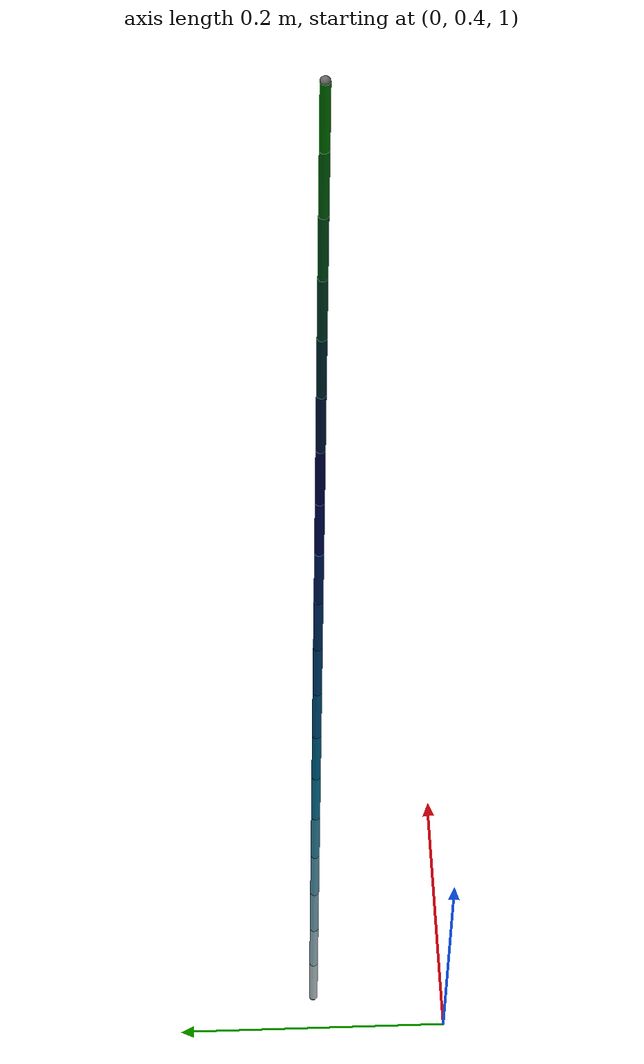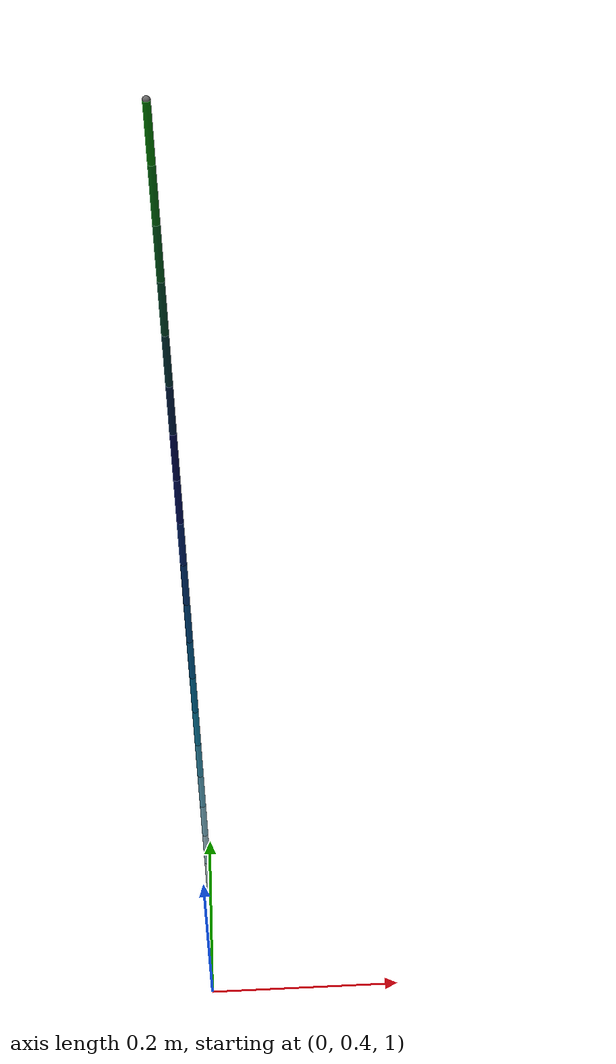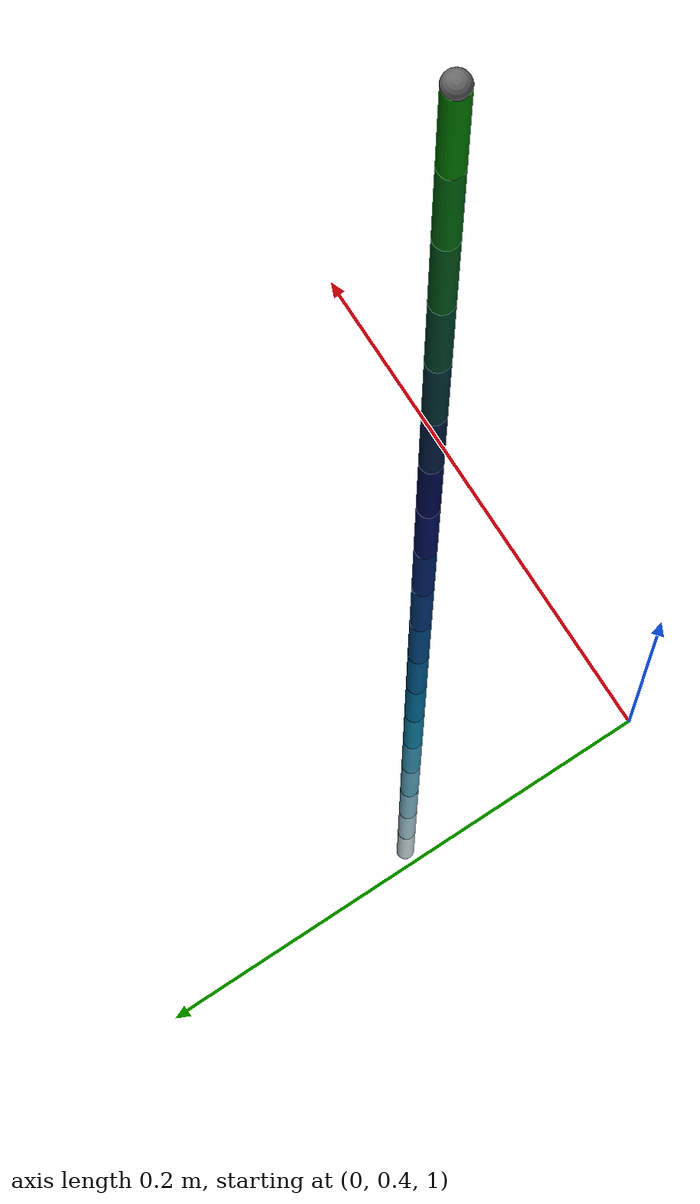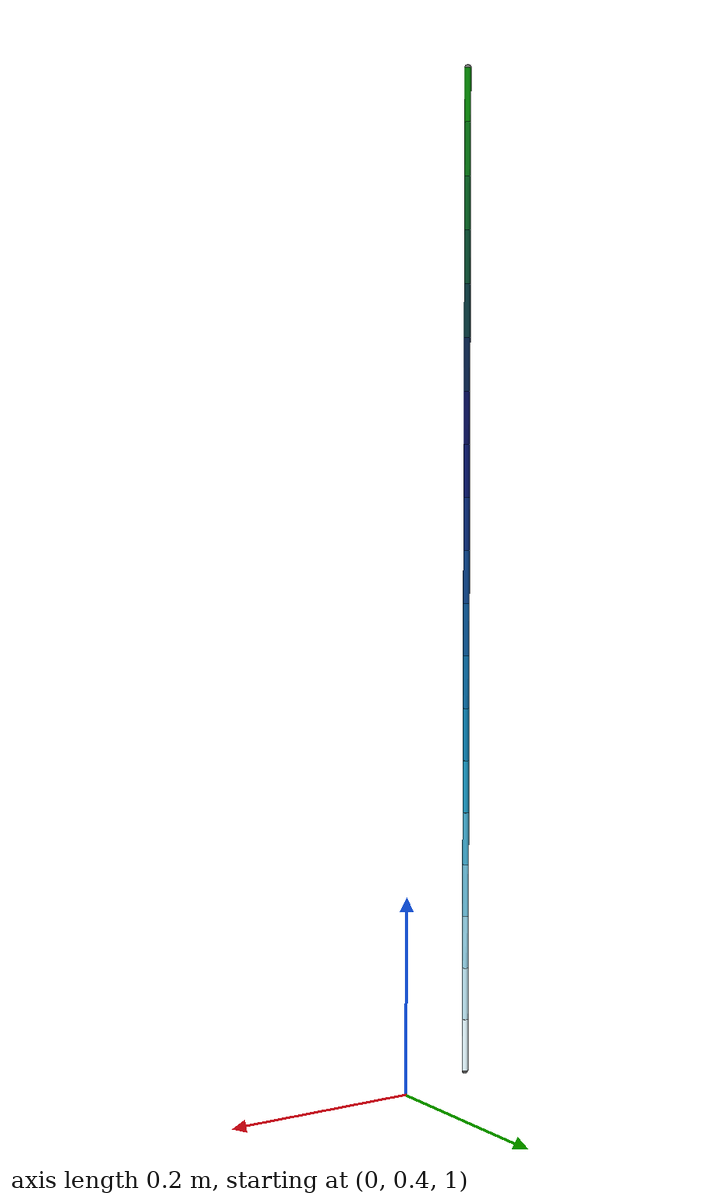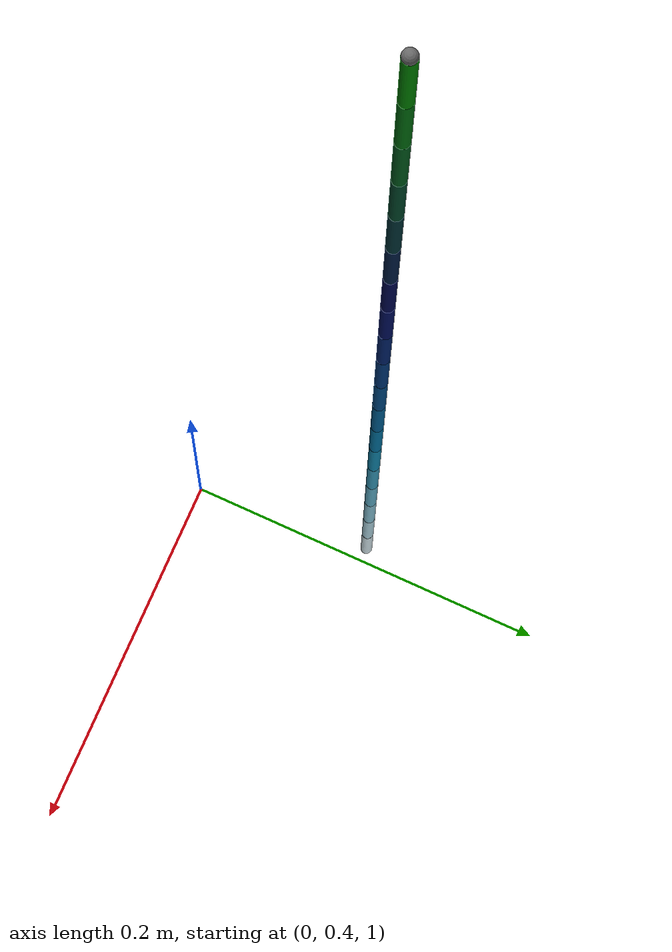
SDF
<sdf version='1.6'>
	<model name='model'>
  <link name="model_capsule_1">
      <pose> 0 0.5 2.0 0 0 0</pose>
      <inertial>
        <pose frame=''>0 0 -0.025 0 0 0</pose>
        <mass>0.02</mass>
        <inertia>
          <ixx>4.211666666666667e-06</ixx>
          <ixy>0</ixy>
          <ixz>0</ixz>
          <iyy>4.211666666666667e-06</iyy>
          <iyz>0</iyz>
          <izz>9e-08</izz>
        </inertia>
      </inertial>
      <visual name='cylinder'>
        <pose frame=''> 0 0 -0.025 0 0 0 </pose>
        <geometry>
          <cylinder>
          <radius>0.003</radius>
          <length>0.05</length>
          </cylinder>
        </geometry>
        <material>
          <diffuse>0.0 0.5 0.0 1.0</diffuse>
        </material>
      </visual>

      <visual name='ball_1'>
        <pose frame=''> 0 0 0 0 0 0 </pose>
        <geometry>
          <sphere>
          <radius>0.003</radius>
          </sphere>
        </geometry>
        <material>
          <diffuse>0.4 0.4 0.4 1.0</diffuse>
        </material>
      </visual>

      <visual name='ball_2'>
        <pose frame=''> 0 0 -0.05 0 0 0 </pose>
        <geometry>
          <sphere>
          <radius>0.003</radius>
          </sphere>
        </geometry>
        <material>
          <diffuse>0.4 0.4 0.4 1.0</diffuse>
        </material>
      </visual>

      <collision name='model_capsule_1_cylinder'>
        <pose frame=''> 0 0 -0.025 0 0 0 </pose>
        <geometry>
          <cylinder>
          <radius>0.003</radius>
          <length>0.05</length>
          </cylinder>
        </geometry>

        <surface>
          <friction>
          <ode>
            <mu>0.5</mu>
            <mu2>0.5</mu2>
          </ode>
          </friction>
        </surface>
      </collision>

      <!-- TODO: Put collision here -->
  </link>
  <link name="model_capsule_2">
      <pose> 0 0.5 1.95 0 0 0</pose>
      <inertial>
        <pose frame=''>0 0 -0.025 0 0 0</pose>
        <mass>0.02</mass>
        <inertia>
          <ixx>4.211666666666667e-06</ixx>
          <ixy>0</ixy>
          <ixz>0</ixz>
          <iyy>4.211666666666667e-06</iyy>
          <iyz>0</iyz>
          <izz>9e-08</izz>
        </inertia>
      </inertial>
      <visual name='cylinder'>
        <pose frame=''> 0 0 -0.025 0 0 0 </pose>
        <geometry>
          <cylinder>
          <radius>0.003</radius>
          <length>0.05</length>
          </cylinder>
        </geometry>
        <material>
          <diffuse>0.0 0.4235294117647059 0.050980392156862744 1.0</diffuse>
        </material>
      </visual>

      <visual name='ball_1'>
        <pose frame=''> 0 0 0 0 0 0 </pose>
        <geometry>
          <sphere>
          <radius>0.003</radius>
          </sphere>
        </geometry>
        <material>
          <diffuse>0.4 0.4 0.4 1.0</diffuse>
        </material>
      </visual>

      <visual name='ball_2'>
        <pose frame=''> 0 0 -0.05 0 0 0 </pose>
        <geometry>
          <sphere>
          <radius>0.003</radius>
          </sphere>
        </geometry>
        <material>
          <diffuse>0.4 0.4 0.4 1.0</diffuse>
        </material>
      </visual>

      <collision name='model_capsule_2_cylinder'>
        <pose frame=''> 0 0 -0.025 0 0 0 </pose>
        <geometry>
          <cylinder>
          <radius>0.003</radius>
          <length>0.05</length>
          </cylinder>
        </geometry>

        <surface>
          <friction>
          <ode>
            <mu>0.5</mu>
            <mu2>0.5</mu2>
          </ode>
          </friction>
        </surface>
      </collision>

      <!-- TODO: Put collision here -->
  </link>
  <link name="model_capsule_1_extra">
    <pose> 0 0.5 1.95 0 0 0</pose>
    <inertial>
      <!-- HACK: inertias are not consistent -->
      <mass>1e-6</mass>
      <inertia>
        <ixx>1e-6</ixx>
        <ixy>0</ixy>
        <ixz>0</ixz>
        <iyy>1e-6</iyy>
        <iyz>0</iyz>
        <izz>1e-6</izz>
      </inertia>
    </inertial>
  </link>
  <joint name="model_capsule_1_model_capsule_2_joint_x" type="revolute">
    <pose> 0 0 0 0 0 0 </pose>
    <child>model_capsule_2</child>
    <parent>model_capsule_1_extra</parent>
    <axis>
      <xyz> 1 0 0 </xyz>
      <limit>
        <effort>0</effort>
        <lower>-1</lower>
        <upper>1</upper>
      </limit>
      <dynamics>
        <damping> 0.001 </damping>
        <friction> 0 </friction>
        <spring_reference> 0 </spring_reference>
        <spring_stiffness> 0.1 </spring_stiffness>
      </dynamics>
      <use_parent_model_frame>1</use_parent_model_frame>
    </axis>
  </joint>

  <joint name="model_capsule_1_model_capsule_2_joint_y" type="revolute">
    <pose> 0 0 0 0 0 0 </pose>
    <child>model_capsule_1_extra</child>
    <parent>model_capsule_1</parent>
    <axis>
      <xyz> 0 1 0 </xyz>
      <limit>
        <effort>0</effort>
        <lower>-1</lower>
        <upper>1</upper>
      </limit>
      <dynamics>
        <damping> 0.001 </damping>
        <friction> 0 </friction>
        <spring_reference> 0 </spring_reference>
        <spring_stiffness> 0.1 </spring_stiffness>
      </dynamics>
      <use_parent_model_frame>1</use_parent_model_frame>
    </axis>
  </joint>
<link name="model_capsule_3">
      <pose> 0 0.5 1.9 0 0 0</pose>
      <inertial>
        <pose frame=''>0 0 -0.025 0 0 0</pose>
        <mass>0.02</mass>
        <inertia>
          <ixx>4.211666666666667e-06</ixx>
          <ixy>0</ixy>
          <ixz>0</ixz>
          <iyy>4.211666666666667e-06</iyy>
          <iyz>0</iyz>
          <izz>9e-08</izz>
        </inertia>
      </inertial>
      <visual name='cylinder'>
        <pose frame=''> 0 0 -0.025 0 0 0 </pose>
        <geometry>
          <cylinder>
          <radius>0.003</radius>
          <length>0.05</length>
          </cylinder>
        </geometry>
        <material>
          <diffuse>0.0 0.34705882352941175 0.10196078431372549 1.0</diffuse>
        </material>
      </visual>

      <visual name='ball_1'>
        <pose frame=''> 0 0 0 0 0 0 </pose>
        <geometry>
          <sphere>
          <radius>0.003</radius>
          </sphere>
        </geometry>
        <material>
          <diffuse>0.4 0.4 0.4 1.0</diffuse>
        </material>
      </visual>

      <visual name='ball_2'>
        <pose frame=''> 0 0 -0.05 0 0 0 </pose>
        <geometry>
          <sphere>
          <radius>0.003</radius>
          </sphere>
        </geometry>
        <material>
          <diffuse>0.4 0.4 0.4 1.0</diffuse>
        </material>
      </visual>

      <collision name='model_capsule_3_cylinder'>
        <pose frame=''> 0 0 -0.025 0 0 0 </pose>
        <geometry>
          <cylinder>
          <radius>0.003</radius>
          <length>0.05</length>
          </cylinder>
        </geometry>

        <surface>
          <friction>
          <ode>
            <mu>0.5</mu>
            <mu2>0.5</mu2>
          </ode>
          </friction>
        </surface>
      </collision>

      <!-- TODO: Put collision here -->
  </link>
  <link name="model_capsule_2_extra">
    <pose> 0 0.5 1.9 0 0 0</pose>
    <inertial>
      <!-- HACK: inertias are not consistent -->
      <mass>1e-6</mass>
      <inertia>
        <ixx>1e-6</ixx>
        <ixy>0</ixy>
        <ixz>0</ixz>
        <iyy>1e-6</iyy>
        <iyz>0</iyz>
        <izz>1e-6</izz>
      </inertia>
    </inertial>
  </link>
  <joint name="model_capsule_2_model_capsule_3_joint_x" type="revolute">
    <pose> 0 0 0 0 0 0 </pose>
    <child>model_capsule_3</child>
    <parent>model_capsule_2_extra</parent>
    <axis>
      <xyz> 1 0 0 </xyz>
      <limit>
        <effort>0</effort>
        <lower>-1</lower>
        <upper>1</upper>
      </limit>
      <dynamics>
        <damping> 0.001 </damping>
        <friction> 0 </friction>
        <spring_reference> 0 </spring_reference>
        <spring_stiffness> 0.1 </spring_stiffness>
      </dynamics>
      <use_parent_model_frame>1</use_parent_model_frame>
    </axis>
  </joint>

  <joint name="model_capsule_2_model_capsule_3_joint_y" type="revolute">
    <pose> 0 0 0 0 0 0 </pose>
    <child>model_capsule_2_extra</child>
    <parent>model_capsule_2</parent>
    <axis>
      <xyz> 0 1 0 </xyz>
      <limit>
        <effort>0</effort>
        <lower>-1</lower>
        <upper>1</upper>
      </limit>
      <dynamics>
        <damping> 0.001 </damping>
        <friction> 0 </friction>
        <spring_reference> 0 </spring_reference>
        <spring_stiffness> 0.1 </spring_stiffness>
      </dynamics>
      <use_parent_model_frame>1</use_parent_model_frame>
    </axis>
  </joint>
<link name="model_capsule_4">
      <pose> 0 0.5 1.8499999999999999 0 0 0</pose>
      <inertial>
        <pose frame=''>0 0 -0.025 0 0 0</pose>
        <mass>0.02</mass>
        <inertia>
          <ixx>4.211666666666667e-06</ixx>
          <ixy>0</ixy>
          <ixz>0</ixz>
          <iyy>4.211666666666667e-06</iyy>
          <iyz>0</iyz>
          <izz>9e-08</izz>
        </inertia>
      </inertial>
      <visual name='cylinder'>
        <pose frame=''> 0 0 -0.025 0 0 0 </pose>
        <geometry>
          <cylinder>
          <radius>0.003</radius>
          <length>0.05</length>
          </cylinder>
        </geometry>
        <material>
          <diffuse>0.0 0.2647058823529412 0.1568627450980392 1.0</diffuse>
        </material>
      </visual>

      <visual name='ball_1'>
        <pose frame=''> 0 0 0 0 0 0 </pose>
        <geometry>
          <sphere>
          <radius>0.003</radius>
          </sphere>
        </geometry>
        <material>
          <diffuse>0.4 0.4 0.4 1.0</diffuse>
        </material>
      </visual>

      <visual name='ball_2'>
        <pose frame=''> 0 0 -0.05 0 0 0 </pose>
        <geometry>
          <sphere>
          <radius>0.003</radius>
          </sphere>
        </geometry>
        <material>
          <diffuse>0.4 0.4 0.4 1.0</diffuse>
        </material>
      </visual>

      <collision name='model_capsule_4_cylinder'>
        <pose frame=''> 0 0 -0.025 0 0 0 </pose>
        <geometry>
          <cylinder>
          <radius>0.003</radius>
          <length>0.05</length>
          </cylinder>
        </geometry>

        <surface>
          <friction>
          <ode>
            <mu>0.5</mu>
            <mu2>0.5</mu2>
          </ode>
          </friction>
        </surface>
      </collision>

      <!-- TODO: Put collision here -->
  </link>
  <link name="model_capsule_3_extra">
    <pose> 0 0.5 1.8499999999999999 0 0 0</pose>
    <inertial>
      <!-- HACK: inertias are not consistent -->
      <mass>1e-6</mass>
      <inertia>
        <ixx>1e-6</ixx>
        <ixy>0</ixy>
        <ixz>0</ixz>
        <iyy>1e-6</iyy>
        <iyz>0</iyz>
        <izz>1e-6</izz>
      </inertia>
    </inertial>
  </link>
  <joint name="model_capsule_3_model_capsule_4_joint_x" type="revolute">
    <pose> 0 0 0 0 0 0 </pose>
    <child>model_capsule_4</child>
    <parent>model_capsule_3_extra</parent>
    <axis>
      <xyz> 1 0 0 </xyz>
      <limit>
        <effort>0</effort>
        <lower>-1</lower>
        <upper>1</upper>
      </limit>
      <dynamics>
        <damping> 0.001 </damping>
        <friction> 0 </friction>
        <spring_reference> 0 </spring_reference>
        <spring_stiffness> 0.1 </spring_stiffness>
      </dynamics>
      <use_parent_model_frame>1</use_parent_model_frame>
    </axis>
  </joint>

  <joint name="model_capsule_3_model_capsule_4_joint_y" type="revolute">
    <pose> 0 0 0 0 0 0 </pose>
    <child>model_capsule_3_extra</child>
    <parent>model_capsule_3</parent>
    <axis>
      <xyz> 0 1 0 </xyz>
      <limit>
        <effort>0</effort>
        <lower>-1</lower>
        <upper>1</upper>
      </limit>
      <dynamics>
        <damping> 0.001 </damping>
        <friction> 0 </friction>
        <spring_reference> 0 </spring_reference>
        <spring_stiffness> 0.1 </spring_stiffness>
      </dynamics>
      <use_parent_model_frame>1</use_parent_model_frame>
    </axis>
  </joint>
<link name="model_capsule_5">
      <pose> 0 0.5 1.7999999999999998 0 0 0</pose>
      <inertial>
        <pose frame=''>0 0 -0.025 0 0 0</pose>
        <mass>0.02</mass>
        <inertia>
          <ixx>4.211666666666667e-06</ixx>
          <ixy>0</ixy>
          <ixz>0</ixz>
          <iyy>4.211666666666667e-06</iyy>
          <iyz>0</iyz>
          <izz>9e-08</izz>
        </inertia>
      </inertial>
      <visual name='cylinder'>
        <pose frame=''> 0 0 -0.025 0 0 0 </pose>
        <geometry>
          <cylinder>
          <radius>0.003</radius>
          <length>0.05</length>
          </cylinder>
        </geometry>
        <material>
          <diffuse>0.0 0.18823529411764706 0.20784313725490194 1.0</diffuse>
        </material>
      </visual>

      <visual name='ball_1'>
        <pose frame=''> 0 0 0 0 0 0 </pose>
        <geometry>
          <sphere>
          <radius>0.003</radius>
          </sphere>
        </geometry>
        <material>
          <diffuse>0.4 0.4 0.4 1.0</diffuse>
        </material>
      </visual>

      <visual name='ball_2'>
        <pose frame=''> 0 0 -0.05 0 0 0 </pose>
        <geometry>
          <sphere>
          <radius>0.003</radius>
          </sphere>
        </geometry>
        <material>
          <diffuse>0.4 0.4 0.4 1.0</diffuse>
        </material>
      </visual>

      <collision name='model_capsule_5_cylinder'>
        <pose frame=''> 0 0 -0.025 0 0 0 </pose>
        <geometry>
          <cylinder>
          <radius>0.003</radius>
          <length>0.05</length>
          </cylinder>
        </geometry>

        <surface>
          <friction>
          <ode>
            <mu>0.5</mu>
            <mu2>0.5</mu2>
          </ode>
          </friction>
        </surface>
      </collision>

      <!-- TODO: Put collision here -->
  </link>
  <link name="model_capsule_4_extra">
    <pose> 0 0.5 1.7999999999999998 0 0 0</pose>
    <inertial>
      <!-- HACK: inertias are not consistent -->
      <mass>1e-6</mass>
      <inertia>
        <ixx>1e-6</ixx>
        <ixy>0</ixy>
        <ixz>0</ixz>
        <iyy>1e-6</iyy>
        <iyz>0</iyz>
        <izz>1e-6</izz>
      </inertia>
    </inertial>
  </link>
  <joint name="model_capsule_4_model_capsule_5_joint_x" type="revolute">
    <pose> 0 0 0 0 0 0 </pose>
    <child>model_capsule_5</child>
    <parent>model_capsule_4_extra</parent>
    <axis>
      <xyz> 1 0 0 </xyz>
      <limit>
        <effort>0</effort>
        <lower>-1</lower>
        <upper>1</upper>
      </limit>
      <dynamics>
        <damping> 0.001 </damping>
        <friction> 0 </friction>
        <spring_reference> 0 </spring_reference>
        <spring_stiffness> 0.1 </spring_stiffness>
      </dynamics>
      <use_parent_model_frame>1</use_parent_model_frame>
    </axis>
  </joint>

  <joint name="model_capsule_4_model_capsule_5_joint_y" type="revolute">
    <pose> 0 0 0 0 0 0 </pose>
    <child>model_capsule_4_extra</child>
    <parent>model_capsule_4</parent>
    <axis>
      <xyz> 0 1 0 </xyz>
      <limit>
        <effort>0</effort>
        <lower>-1</lower>
        <upper>1</upper>
      </limit>
      <dynamics>
        <damping> 0.001 </damping>
        <friction> 0 </friction>
        <spring_reference> 0 </spring_reference>
        <spring_stiffness> 0.1 </spring_stiffness>
      </dynamics>
      <use_parent_model_frame>1</use_parent_model_frame>
    </axis>
  </joint>
<link name="model_capsule_6">
      <pose> 0 0.5 1.7499999999999998 0 0 0</pose>
      <inertial>
        <pose frame=''>0 0 -0.025 0 0 0</pose>
        <mass>0.02</mass>
        <inertia>
          <ixx>4.211666666666667e-06</ixx>
          <ixy>0</ixy>
          <ixz>0</ixz>
          <iyy>4.211666666666667e-06</iyy>
          <iyz>0</iyz>
          <izz>9e-08</izz>
        </inertia>
      </inertial>
      <visual name='cylinder'>
        <pose frame=''> 0 0 -0.025 0 0 0 </pose>
        <geometry>
          <cylinder>
          <radius>0.003</radius>
          <length>0.05</length>
          </cylinder>
        </geometry>
        <material>
          <diffuse>0.0 0.10588235294117643 0.2627450980392157 1.0</diffuse>
        </material>
      </visual>

      <visual name='ball_1'>
        <pose frame=''> 0 0 0 0 0 0 </pose>
        <geometry>
          <sphere>
          <radius>0.003</radius>
          </sphere>
        </geometry>
        <material>
          <diffuse>0.4 0.4 0.4 1.0</diffuse>
        </material>
      </visual>

      <visual name='ball_2'>
        <pose frame=''> 0 0 -0.05 0 0 0 </pose>
        <geometry>
          <sphere>
          <radius>0.003</radius>
          </sphere>
        </geometry>
        <material>
          <diffuse>0.4 0.4 0.4 1.0</diffuse>
        </material>
      </visual>

      <collision name='model_capsule_6_cylinder'>
        <pose frame=''> 0 0 -0.025 0 0 0 </pose>
        <geometry>
          <cylinder>
          <radius>0.003</radius>
          <length>0.05</length>
          </cylinder>
        </geometry>

        <surface>
          <friction>
          <ode>
            <mu>0.5</mu>
            <mu2>0.5</mu2>
          </ode>
          </friction>
        </surface>
      </collision>

      <!-- TODO: Put collision here -->
  </link>
  <link name="model_capsule_5_extra">
    <pose> 0 0.5 1.7499999999999998 0 0 0</pose>
    <inertial>
      <!-- HACK: inertias are not consistent -->
      <mass>1e-6</mass>
      <inertia>
        <ixx>1e-6</ixx>
        <ixy>0</ixy>
        <ixz>0</ixz>
        <iyy>1e-6</iyy>
        <iyz>0</iyz>
        <izz>1e-6</izz>
      </inertia>
    </inertial>
  </link>
  <joint name="model_capsule_5_model_capsule_6_joint_x" type="revolute">
    <pose> 0 0 0 0 0 0 </pose>
    <child>model_capsule_6</child>
    <parent>model_capsule_5_extra</parent>
    <axis>
      <xyz> 1 0 0 </xyz>
      <limit>
        <effort>0</effort>
        <lower>-1</lower>
        <upper>1</upper>
      </limit>
      <dynamics>
        <damping> 0.001 </damping>
        <friction> 0 </friction>
        <spring_reference> 0 </spring_reference>
        <spring_stiffness> 0.1 </spring_stiffness>
      </dynamics>
      <use_parent_model_frame>1</use_parent_model_frame>
    </axis>
  </joint>

  <joint name="model_capsule_5_model_capsule_6_joint_y" type="revolute">
    <pose> 0 0 0 0 0 0 </pose>
    <child>model_capsule_5_extra</child>
    <parent>model_capsule_5</parent>
    <axis>
      <xyz> 0 1 0 </xyz>
      <limit>
        <effort>0</effort>
        <lower>-1</lower>
        <upper>1</upper>
      </limit>
      <dynamics>
        <damping> 0.001 </damping>
        <friction> 0 </friction>
        <spring_reference> 0 </spring_reference>
        <spring_stiffness> 0.1 </spring_stiffness>
      </dynamics>
      <use_parent_model_frame>1</use_parent_model_frame>
    </axis>
  </joint>
<link name="model_capsule_7">
      <pose> 0 0.5 1.6999999999999997 0 0 0</pose>
      <inertial>
        <pose frame=''>0 0 -0.025 0 0 0</pose>
        <mass>0.02</mass>
        <inertia>
          <ixx>4.211666666666667e-06</ixx>
          <ixy>0</ixy>
          <ixz>0</ixz>
          <iyy>4.211666666666667e-06</iyy>
          <iyz>0</iyz>
          <izz>9e-08</izz>
        </inertia>
      </inertial>
      <visual name='cylinder'>
        <pose frame=''> 0 0 -0.025 0 0 0 </pose>
        <geometry>
          <cylinder>
          <radius>0.003</radius>
          <length>0.05</length>
          </cylinder>
        </geometry>
        <material>
          <diffuse>0.0 0.02941176470588236 0.3137254901960784 1.0</diffuse>
        </material>
      </visual>

      <visual name='ball_1'>
        <pose frame=''> 0 0 0 0 0 0 </pose>
        <geometry>
          <sphere>
          <radius>0.003</radius>
          </sphere>
        </geometry>
        <material>
          <diffuse>0.4 0.4 0.4 1.0</diffuse>
        </material>
      </visual>

      <visual name='ball_2'>
        <pose frame=''> 0 0 -0.05 0 0 0 </pose>
        <geometry>
          <sphere>
          <radius>0.003</radius>
          </sphere>
        </geometry>
        <material>
          <diffuse>0.4 0.4 0.4 1.0</diffuse>
        </material>
      </visual>

      <collision name='model_capsule_7_cylinder'>
        <pose frame=''> 0 0 -0.025 0 0 0 </pose>
        <geometry>
          <cylinder>
          <radius>0.003</radius>
          <length>0.05</length>
          </cylinder>
        </geometry>

        <surface>
          <friction>
          <ode>
            <mu>0.5</mu>
            <mu2>0.5</mu2>
          </ode>
          </friction>
        </surface>
      </collision>

      <!-- TODO: Put collision here -->
  </link>
  <link name="model_capsule_6_extra">
    <pose> 0 0.5 1.6999999999999997 0 0 0</pose>
    <inertial>
      <!-- HACK: inertias are not consistent -->
      <mass>1e-6</mass>
      <inertia>
        <ixx>1e-6</ixx>
        <ixy>0</ixy>
        <ixz>0</ixz>
        <iyy>1e-6</iyy>
        <iyz>0</iyz>
        <izz>1e-6</izz>
      </inertia>
    </inertial>
  </link>
  <joint name="model_capsule_6_model_capsule_7_joint_x" type="revolute">
    <pose> 0 0 0 0 0 0 </pose>
    <child>model_capsule_7</child>
    <parent>model_capsule_6_extra</parent>
    <axis>
      <xyz> 1 0 0 </xyz>
      <limit>
        <effort>0</effort>
        <lower>-1</lower>
        <upper>1</upper>
      </limit>
      <dynamics>
        <damping> 0.001 </damping>
        <friction> 0 </friction>
        <spring_reference> 0 </spring_reference>
        <spring_stiffness> 0.1 </spring_stiffness>
      </dynamics>
      <use_parent_model_frame>1</use_parent_model_frame>
    </axis>
  </joint>

  <joint name="model_capsule_6_model_capsule_7_joint_y" type="revolute">
    <pose> 0 0 0 0 0 0 </pose>
    <child>model_capsule_6_extra</child>
    <parent>model_capsule_6</parent>
    <axis>
      <xyz> 0 1 0 </xyz>
      <limit>
        <effort>0</effort>
        <lower>-1</lower>
        <upper>1</upper>
      </limit>
      <dynamics>
        <damping> 0.001 </damping>
        <friction> 0 </friction>
        <spring_reference> 0 </spring_reference>
        <spring_stiffness> 0.1 </spring_stiffness>
      </dynamics>
      <use_parent_model_frame>1</use_parent_model_frame>
    </axis>
  </joint>
<link name="model_capsule_8">
      <pose> 0 0.5 1.6499999999999997 0 0 0</pose>
      <inertial>
        <pose frame=''>0 0 -0.025 0 0 0</pose>
        <mass>0.02</mass>
        <inertia>
          <ixx>4.211666666666667e-06</ixx>
          <ixy>0</ixy>
          <ixz>0</ixz>
          <iyy>4.211666666666667e-06</iyy>
          <iyz>0</iyz>
          <izz>9e-08</izz>
        </inertia>
      </inertial>
      <visual name='cylinder'>
        <pose frame=''> 0 0 -0.025 0 0 0 </pose>
        <geometry>
          <cylinder>
          <radius>0.003</radius>
          <length>0.05</length>
          </cylinder>
        </geometry>
        <material>
          <diffuse>0.0 0.05294117647058827 0.3686274509803922 1.0</diffuse>
        </material>
      </visual>

      <visual name='ball_1'>
        <pose frame=''> 0 0 0 0 0 0 </pose>
        <geometry>
          <sphere>
          <radius>0.003</radius>
          </sphere>
        </geometry>
        <material>
          <diffuse>0.4 0.4 0.4 1.0</diffuse>
        </material>
      </visual>

      <visual name='ball_2'>
        <pose frame=''> 0 0 -0.05 0 0 0 </pose>
        <geometry>
          <sphere>
          <radius>0.003</radius>
          </sphere>
        </geometry>
        <material>
          <diffuse>0.4 0.4 0.4 1.0</diffuse>
        </material>
      </visual>

      <collision name='model_capsule_8_cylinder'>
        <pose frame=''> 0 0 -0.025 0 0 0 </pose>
        <geometry>
          <cylinder>
          <radius>0.003</radius>
          <length>0.05</length>
          </cylinder>
        </geometry>

        <surface>
          <friction>
          <ode>
            <mu>0.5</mu>
            <mu2>0.5</mu2>
          </ode>
          </friction>
        </surface>
      </collision>

      <!-- TODO: Put collision here -->
  </link>
  <link name="model_capsule_7_extra">
    <pose> 0 0.5 1.6499999999999997 0 0 0</pose>
    <inertial>
      <!-- HACK: inertias are not consistent -->
      <mass>1e-6</mass>
      <inertia>
        <ixx>1e-6</ixx>
        <ixy>0</ixy>
        <ixz>0</ixz>
        <iyy>1e-6</iyy>
        <iyz>0</iyz>
        <izz>1e-6</izz>
      </inertia>
    </inertial>
  </link>
  <joint name="model_capsule_7_model_capsule_8_joint_x" type="revolute">
    <pose> 0 0 0 0 0 0 </pose>
    <child>model_capsule_8</child>
    <parent>model_capsule_7_extra</parent>
    <axis>
      <xyz> 1 0 0 </xyz>
      <limit>
        <effort>0</effort>
        <lower>-1</lower>
        <upper>1</upper>
      </limit>
      <dynamics>
        <damping> 0.001 </damping>
        <friction> 0 </friction>
        <spring_reference> 0 </spring_reference>
        <spring_stiffness> 0.1 </spring_stiffness>
      </dynamics>
      <use_parent_model_frame>1</use_parent_model_frame>
    </axis>
  </joint>

  <joint name="model_capsule_7_model_capsule_8_joint_y" type="revolute">
    <pose> 0 0 0 0 0 0 </pose>
    <child>model_capsule_7_extra</child>
    <parent>model_capsule_7</parent>
    <axis>
      <xyz> 0 1 0 </xyz>
      <limit>
        <effort>0</effort>
        <lower>-1</lower>
        <upper>1</upper>
      </limit>
      <dynamics>
        <damping> 0.001 </damping>
        <friction> 0 </friction>
        <spring_reference> 0 </spring_reference>
        <spring_stiffness> 0.1 </spring_stiffness>
      </dynamics>
      <use_parent_model_frame>1</use_parent_model_frame>
    </axis>
  </joint>
<link name="model_capsule_9">
      <pose> 0 0.5 1.5999999999999996 0 0 0</pose>
      <inertial>
        <pose frame=''>0 0 -0.025 0 0 0</pose>
        <mass>0.02</mass>
        <inertia>
          <ixx>4.211666666666667e-06</ixx>
          <ixy>0</ixy>
          <ixz>0</ixz>
          <iyy>4.211666666666667e-06</iyy>
          <iyz>0</iyz>
          <izz>9e-08</izz>
        </inertia>
      </inertial>
      <visual name='cylinder'>
        <pose frame=''> 0 0 -0.025 0 0 0 </pose>
        <geometry>
          <cylinder>
          <radius>0.003</radius>
          <length>0.05</length>
          </cylinder>
        </geometry>
        <material>
          <diffuse>0.0 0.12941176470588234 0.4196078431372549 1.0</diffuse>
        </material>
      </visual>

      <visual name='ball_1'>
        <pose frame=''> 0 0 0 0 0 0 </pose>
        <geometry>
          <sphere>
          <radius>0.003</radius>
          </sphere>
        </geometry>
        <material>
          <diffuse>0.4 0.4 0.4 1.0</diffuse>
        </material>
      </visual>

      <visual name='ball_2'>
        <pose frame=''> 0 0 -0.05 0 0 0 </pose>
        <geometry>
          <sphere>
          <radius>0.003</radius>
          </sphere>
        </geometry>
        <material>
          <diffuse>0.4 0.4 0.4 1.0</diffuse>
        </material>
      </visual>

      <collision name='model_capsule_9_cylinder'>
        <pose frame=''> 0 0 -0.025 0 0 0 </pose>
        <geometry>
          <cylinder>
          <radius>0.003</radius>
          <length>0.05</length>
          </cylinder>
        </geometry>

        <surface>
          <friction>
          <ode>
            <mu>0.5</mu>
            <mu2>0.5</mu2>
          </ode>
          </friction>
        </surface>
      </collision>

      <!-- TODO: Put collision here -->
  </link>
  <link name="model_capsule_8_extra">
    <pose> 0 0.5 1.5999999999999996 0 0 0</pose>
    <inertial>
      <!-- HACK: inertias are not consistent -->
      <mass>1e-6</mass>
      <inertia>
        <ixx>1e-6</ixx>
        <ixy>0</ixy>
        <ixz>0</ixz>
        <iyy>1e-6</iyy>
        <iyz>0</iyz>
        <izz>1e-6</izz>
      </inertia>
    </inertial>
  </link>
  <joint name="model_capsule_8_model_capsule_9_joint_x" type="revolute">
    <pose> 0 0 0 0 0 0 </pose>
    <child>model_capsule_9</child>
    <parent>model_capsule_8_extra</parent>
    <axis>
      <xyz> 1 0 0 </xyz>
      <limit>
        <effort>0</effort>
        <lower>-1</lower>
        <upper>1</upper>
      </limit>
      <dynamics>
        <damping> 0.001 </damping>
        <friction> 0 </friction>
        <spring_reference> 0 </spring_reference>
        <spring_stiffness> 0.1 </spring_stiffness>
      </dynamics>
      <use_parent_model_frame>1</use_parent_model_frame>
    </axis>
  </joint>

  <joint name="model_capsule_8_model_capsule_9_joint_y" type="revolute">
    <pose> 0 0 0 0 0 0 </pose>
    <child>model_capsule_8_extra</child>
    <parent>model_capsule_8</parent>
    <axis>
      <xyz> 0 1 0 </xyz>
      <limit>
        <effort>0</effort>
        <lower>-1</lower>
        <upper>1</upper>
      </limit>
      <dynamics>
        <damping> 0.001 </damping>
        <friction> 0 </friction>
        <spring_reference> 0 </spring_reference>
        <spring_stiffness> 0.1 </spring_stiffness>
      </dynamics>
      <use_parent_model_frame>1</use_parent_model_frame>
    </axis>
  </joint>
<link name="model_capsule_10">
      <pose> 0 0.5 1.5499999999999996 0 0 0</pose>
      <inertial>
        <pose frame=''>0 0 -0.025 0 0 0</pose>
        <mass>0.02</mass>
        <inertia>
          <ixx>4.211666666666667e-06</ixx>
          <ixy>0</ixy>
          <ixz>0</ixz>
          <iyy>4.211666666666667e-06</iyy>
          <iyz>0</iyz>
          <izz>9e-08</izz>
        </inertia>
      </inertial>
      <visual name='cylinder'>
        <pose frame=''> 0 0 -0.025 0 0 0 </pose>
        <geometry>
          <cylinder>
          <radius>0.003</radius>
          <length>0.05</length>
          </cylinder>
        </geometry>
        <material>
          <diffuse>0.0 0.21176470588235285 0.4745098039215686 1.0</diffuse>
        </material>
      </visual>

      <visual name='ball_1'>
        <pose frame=''> 0 0 0 0 0 0 </pose>
        <geometry>
          <sphere>
          <radius>0.003</radius>
          </sphere>
        </geometry>
        <material>
          <diffuse>0.4 0.4 0.4 1.0</diffuse>
        </material>
      </visual>

      <visual name='ball_2'>
        <pose frame=''> 0 0 -0.05 0 0 0 </pose>
        <geometry>
          <sphere>
          <radius>0.003</radius>
          </sphere>
        </geometry>
        <material>
          <diffuse>0.4 0.4 0.4 1.0</diffuse>
        </material>
      </visual>

      <collision name='model_capsule_10_cylinder'>
        <pose frame=''> 0 0 -0.025 0 0 0 </pose>
        <geometry>
          <cylinder>
          <radius>0.003</radius>
          <length>0.05</length>
          </cylinder>
        </geometry>

        <surface>
          <friction>
          <ode>
            <mu>0.5</mu>
            <mu2>0.5</mu2>
          </ode>
          </friction>
        </surface>
      </collision>

      <!-- TODO: Put collision here -->
  </link>
  <link name="model_capsule_9_extra">
    <pose> 0 0.5 1.5499999999999996 0 0 0</pose>
    <inertial>
      <!-- HACK: inertias are not consistent -->
      <mass>1e-6</mass>
      <inertia>
        <ixx>1e-6</ixx>
        <ixy>0</ixy>
        <ixz>0</ixz>
        <iyy>1e-6</iyy>
        <iyz>0</iyz>
        <izz>1e-6</izz>
      </inertia>
    </inertial>
  </link>
  <joint name="model_capsule_9_model_capsule_10_joint_x" type="revolute">
    <pose> 0 0 0 0 0 0 </pose>
    <child>model_capsule_10</child>
    <parent>model_capsule_9_extra</parent>
    <axis>
      <xyz> 1 0 0 </xyz>
      <limit>
        <effort>0</effort>
        <lower>-1</lower>
        <upper>1</upper>
      </limit>
      <dynamics>
        <damping> 0.001 </damping>
        <friction> 0 </friction>
        <spring_reference> 0 </spring_reference>
        <spring_stiffness> 0.1 </spring_stiffness>
      </dynamics>
      <use_parent_model_frame>1</use_parent_model_frame>
    </axis>
  </joint>

  <joint name="model_capsule_9_model_capsule_10_joint_y" type="revolute">
    <pose> 0 0 0 0 0 0 </pose>
    <child>model_capsule_9_extra</child>
    <parent>model_capsule_9</parent>
    <axis>
      <xyz> 0 1 0 </xyz>
      <limit>
        <effort>0</effort>
        <lower>-1</lower>
        <upper>1</upper>
      </limit>
      <dynamics>
        <damping> 0.001 </damping>
        <friction> 0 </friction>
        <spring_reference> 0 </spring_reference>
        <spring_stiffness> 0.1 </spring_stiffness>
      </dynamics>
      <use_parent_model_frame>1</use_parent_model_frame>
    </axis>
  </joint>
<link name="model_capsule_11">
      <pose> 0 0.5 1.4999999999999996 0 0 0</pose>
      <inertial>
        <pose frame=''>0 0 -0.025 0 0 0</pose>
        <mass>0.02</mass>
        <inertia>
          <ixx>4.211666666666667e-06</ixx>
          <ixy>0</ixy>
          <ixz>0</ixz>
          <iyy>4.211666666666667e-06</iyy>
          <iyz>0</iyz>
          <izz>9e-08</izz>
        </inertia>
      </inertial>
      <visual name='cylinder'>
        <pose frame=''> 0 0 -0.025 0 0 0 </pose>
        <geometry>
          <cylinder>
          <radius>0.003</radius>
          <length>0.05</length>
          </cylinder>
        </geometry>
        <material>
          <diffuse>0.0 0.28823529411764715 0.5254901960784314 1.0</diffuse>
        </material>
      </visual>

      <visual name='ball_1'>
        <pose frame=''> 0 0 0 0 0 0 </pose>
        <geometry>
          <sphere>
          <radius>0.003</radius>
          </sphere>
        </geometry>
        <material>
          <diffuse>0.4 0.4 0.4 1.0</diffuse>
        </material>
      </visual>

      <visual name='ball_2'>
        <pose frame=''> 0 0 -0.05 0 0 0 </pose>
        <geometry>
          <sphere>
          <radius>0.003</radius>
          </sphere>
        </geometry>
        <material>
          <diffuse>0.4 0.4 0.4 1.0</diffuse>
        </material>
      </visual>

      <collision name='model_capsule_11_cylinder'>
        <pose frame=''> 0 0 -0.025 0 0 0 </pose>
        <geometry>
          <cylinder>
          <radius>0.003</radius>
          <length>0.05</length>
          </cylinder>
        </geometry>

        <surface>
          <friction>
          <ode>
            <mu>0.5</mu>
            <mu2>0.5</mu2>
          </ode>
          </friction>
        </surface>
      </collision>

      <!-- TODO: Put collision here -->
  </link>
  <link name="model_capsule_10_extra">
    <pose> 0 0.5 1.4999999999999996 0 0 0</pose>
    <inertial>
      <!-- HACK: inertias are not consistent -->
      <mass>1e-6</mass>
      <inertia>
        <ixx>1e-6</ixx>
        <ixy>0</ixy>
        <ixz>0</ixz>
        <iyy>1e-6</iyy>
        <iyz>0</iyz>
        <izz>1e-6</izz>
      </inertia>
    </inertial>
  </link>
  <joint name="model_capsule_10_model_capsule_11_joint_x" type="revolute">
    <pose> 0 0 0 0 0 0 </pose>
    <child>model_capsule_11</child>
    <parent>model_capsule_10_extra</parent>
    <axis>
      <xyz> 1 0 0 </xyz>
      <limit>
        <effort>0</effort>
        <lower>-1</lower>
        <upper>1</upper>
      </limit>
      <dynamics>
        <damping> 0.001 </damping>
        <friction> 0 </friction>
        <spring_reference> 0 </spring_reference>
        <spring_stiffness> 0.1 </spring_stiffness>
      </dynamics>
      <use_parent_model_frame>1</use_parent_model_frame>
    </axis>
  </joint>

  <joint name="model_capsule_10_model_capsule_11_joint_y" type="revolute">
    <pose> 0 0 0 0 0 0 </pose>
    <child>model_capsule_10_extra</child>
    <parent>model_capsule_10</parent>
    <axis>
      <xyz> 0 1 0 </xyz>
      <limit>
        <effort>0</effort>
        <lower>-1</lower>
        <upper>1</upper>
      </limit>
      <dynamics>
        <damping> 0.001 </damping>
        <friction> 0 </friction>
        <spring_reference> 0 </spring_reference>
        <spring_stiffness> 0.1 </spring_stiffness>
      </dynamics>
      <use_parent_model_frame>1</use_parent_model_frame>
    </axis>
  </joint>
<link name="model_capsule_12">
      <pose> 0 0.5 1.4499999999999995 0 0 0</pose>
      <inertial>
        <pose frame=''>0 0 -0.025 0 0 0</pose>
        <mass>0.02</mass>
        <inertia>
          <ixx>4.211666666666667e-06</ixx>
          <ixy>0</ixy>
          <ixz>0</ixz>
          <iyy>4.211666666666667e-06</iyy>
          <iyz>0</iyz>
          <izz>9e-08</izz>
        </inertia>
      </inertial>
      <visual name='cylinder'>
        <pose frame=''> 0 0 -0.025 0 0 0 </pose>
        <geometry>
          <cylinder>
          <radius>0.003</radius>
          <length>0.05</length>
          </cylinder>
        </geometry>
        <material>
          <diffuse>0.0 0.37058823529411755 0.580392156862745 1.0</diffuse>
        </material>
      </visual>

      <visual name='ball_1'>
        <pose frame=''> 0 0 0 0 0 0 </pose>
        <geometry>
          <sphere>
          <radius>0.003</radius>
          </sphere>
        </geometry>
        <material>
          <diffuse>0.4 0.4 0.4 1.0</diffuse>
        </material>
      </visual>

      <visual name='ball_2'>
        <pose frame=''> 0 0 -0.05 0 0 0 </pose>
        <geometry>
          <sphere>
          <radius>0.003</radius>
          </sphere>
        </geometry>
        <material>
          <diffuse>0.4 0.4 0.4 1.0</diffuse>
        </material>
      </visual>

      <collision name='model_capsule_12_cylinder'>
        <pose frame=''> 0 0 -0.025 0 0 0 </pose>
        <geometry>
          <cylinder>
          <radius>0.003</radius>
          <length>0.05</length>
          </cylinder>
        </geometry>

        <surface>
          <friction>
          <ode>
            <mu>0.5</mu>
            <mu2>0.5</mu2>
          </ode>
          </friction>
        </surface>
      </collision>

      <!-- TODO: Put collision here -->
  </link>
  <link name="model_capsule_11_extra">
    <pose> 0 0.5 1.4499999999999995 0 0 0</pose>
    <inertial>
      <!-- HACK: inertias are not consistent -->
      <mass>1e-6</mass>
      <inertia>
        <ixx>1e-6</ixx>
        <ixy>0</ixy>
        <ixz>0</ixz>
        <iyy>1e-6</iyy>
        <iyz>0</iyz>
        <izz>1e-6</izz>
      </inertia>
    </inertial>
  </link>
  <joint name="model_capsule_11_model_capsule_12_joint_x" type="revolute">
    <pose> 0 0 0 0 0 0 </pose>
    <child>model_capsule_12</child>
    <parent>model_capsule_11_extra</parent>
    <axis>
      <xyz> 1 0 0 </xyz>
      <limit>
        <effort>0</effort>
        <lower>-1</lower>
        <upper>1</upper>
      </limit>
      <dynamics>
        <damping> 0.001 </damping>
        <friction> 0 </friction>
        <spring_reference> 0 </spring_reference>
        <spring_stiffness> 0.1 </spring_stiffness>
      </dynamics>
      <use_parent_model_frame>1</use_parent_model_frame>
    </axis>
  </joint>

  <joint name="model_capsule_11_model_capsule_12_joint_y" type="revolute">
    <pose> 0 0 0 0 0 0 </pose>
    <child>model_capsule_11_extra</child>
    <parent>model_capsule_11</parent>
    <axis>
      <xyz> 0 1 0 </xyz>
      <limit>
        <effort>0</effort>
        <lower>-1</lower>
        <upper>1</upper>
      </limit>
      <dynamics>
        <damping> 0.001 </damping>
        <friction> 0 </friction>
        <spring_reference> 0 </spring_reference>
        <spring_stiffness> 0.1 </spring_stiffness>
      </dynamics>
      <use_parent_model_frame>1</use_parent_model_frame>
    </axis>
  </joint>
<link name="model_capsule_13">
      <pose> 0 0.5 1.3999999999999995 0 0 0</pose>
      <inertial>
        <pose frame=''>0 0 -0.025 0 0 0</pose>
        <mass>0.02</mass>
        <inertia>
          <ixx>4.211666666666667e-06</ixx>
          <ixy>0</ixy>
          <ixz>0</ixz>
          <iyy>4.211666666666667e-06</iyy>
          <iyz>0</iyz>
          <izz>9e-08</izz>
        </inertia>
      </inertial>
      <visual name='cylinder'>
        <pose frame=''> 0 0 -0.025 0 0 0 </pose>
        <geometry>
          <cylinder>
          <radius>0.003</radius>
          <length>0.05</length>
          </cylinder>
        </geometry>
        <material>
          <diffuse>0.0 0.44705882352941173 0.6313725490196078 1.0</diffuse>
        </material>
      </visual>

      <visual name='ball_1'>
        <pose frame=''> 0 0 0 0 0 0 </pose>
        <geometry>
          <sphere>
          <radius>0.003</radius>
          </sphere>
        </geometry>
        <material>
          <diffuse>0.4 0.4 0.4 1.0</diffuse>
        </material>
      </visual>

      <visual name='ball_2'>
        <pose frame=''> 0 0 -0.05 0 0 0 </pose>
        <geometry>
          <sphere>
          <radius>0.003</radius>
          </sphere>
        </geometry>
        <material>
          <diffuse>0.4 0.4 0.4 1.0</diffuse>
        </material>
      </visual>

      <collision name='model_capsule_13_cylinder'>
        <pose frame=''> 0 0 -0.025 0 0 0 </pose>
        <geometry>
          <cylinder>
          <radius>0.003</radius>
          <length>0.05</length>
          </cylinder>
        </geometry>

        <surface>
          <friction>
          <ode>
            <mu>0.5</mu>
            <mu2>0.5</mu2>
          </ode>
          </friction>
        </surface>
      </collision>

      <!-- TODO: Put collision here -->
  </link>
  <link name="model_capsule_12_extra">
    <pose> 0 0.5 1.3999999999999995 0 0 0</pose>
    <inertial>
      <!-- HACK: inertias are not consistent -->
      <mass>1e-6</mass>
      <inertia>
        <ixx>1e-6</ixx>
        <ixy>0</ixy>
        <ixz>0</ixz>
        <iyy>1e-6</iyy>
        <iyz>0</iyz>
        <izz>1e-6</izz>
      </inertia>
    </inertial>
  </link>
  <joint name="model_capsule_12_model_capsule_13_joint_x" type="revolute">
    <pose> 0 0 0 0 0 0 </pose>
    <child>model_capsule_13</child>
    <parent>model_capsule_12_extra</parent>
    <axis>
      <xyz> 1 0 0 </xyz>
      <limit>
        <effort>0</effort>
        <lower>-1</lower>
        <upper>1</upper>
      </limit>
      <dynamics>
        <damping> 0.001 </damping>
        <friction> 0 </friction>
        <spring_reference> 0 </spring_reference>
        <spring_stiffness> 0.1 </spring_stiffness>
      </dynamics>
      <use_parent_model_frame>1</use_parent_model_frame>
    </axis>
  </joint>

  <joint name="model_capsule_12_model_capsule_13_joint_y" type="revolute">
    <pose> 0 0 0 0 0 0 </pose>
    <child>model_capsule_12_extra</child>
    <parent>model_capsule_12</parent>
    <axis>
      <xyz> 0 1 0 </xyz>
      <limit>
        <effort>0</effort>
        <lower>-1</lower>
        <upper>1</upper>
      </limit>
      <dynamics>
        <damping> 0.001 </damping>
        <friction> 0 </friction>
        <spring_reference> 0 </spring_reference>
        <spring_stiffness> 0.1 </spring_stiffness>
      </dynamics>
      <use_parent_model_frame>1</use_parent_model_frame>
    </axis>
  </joint>
<link name="model_capsule_14">
      <pose> 0 0.5 1.3499999999999994 0 0 0</pose>
      <inertial>
        <pose frame=''>0 0 -0.025 0 0 0</pose>
        <mass>0.02</mass>
        <inertia>
          <ixx>4.211666666666667e-06</ixx>
          <ixy>0</ixy>
          <ixz>0</ixz>
          <iyy>4.211666666666667e-06</iyy>
          <iyz>0</iyz>
          <izz>9e-08</izz>
        </inertia>
      </inertial>
      <visual name='cylinder'>
        <pose frame=''> 0 0 -0.025 0 0 0 </pose>
        <geometry>
          <cylinder>
          <radius>0.003</radius>
          <length>0.05</length>
          </cylinder>
        </geometry>
        <material>
          <diffuse>0.0588235294117645 0.5294117647058822 0.6862745098039216 1.0</diffuse>
        </material>
      </visual>

      <visual name='ball_1'>
        <pose frame=''> 0 0 0 0 0 0 </pose>
        <geometry>
          <sphere>
          <radius>0.003</radius>
          </sphere>
        </geometry>
        <material>
          <diffuse>0.4 0.4 0.4 1.0</diffuse>
        </material>
      </visual>

      <visual name='ball_2'>
        <pose frame=''> 0 0 -0.05 0 0 0 </pose>
        <geometry>
          <sphere>
          <radius>0.003</radius>
          </sphere>
        </geometry>
        <material>
          <diffuse>0.4 0.4 0.4 1.0</diffuse>
        </material>
      </visual>

      <collision name='model_capsule_14_cylinder'>
        <pose frame=''> 0 0 -0.025 0 0 0 </pose>
        <geometry>
          <cylinder>
          <radius>0.003</radius>
          <length>0.05</length>
          </cylinder>
        </geometry>

        <surface>
          <friction>
          <ode>
            <mu>0.5</mu>
            <mu2>0.5</mu2>
          </ode>
          </friction>
        </surface>
      </collision>

      <!-- TODO: Put collision here -->
  </link>
  <link name="model_capsule_13_extra">
    <pose> 0 0.5 1.3499999999999994 0 0 0</pose>
    <inertial>
      <!-- HACK: inertias are not consistent -->
      <mass>1e-6</mass>
      <inertia>
        <ixx>1e-6</ixx>
        <ixy>0</ixy>
        <ixz>0</ixz>
        <iyy>1e-6</iyy>
        <iyz>0</iyz>
        <izz>1e-6</izz>
      </inertia>
    </inertial>
  </link>
  <joint name="model_capsule_13_model_capsule_14_joint_x" type="revolute">
    <pose> 0 0 0 0 0 0 </pose>
    <child>model_capsule_14</child>
    <parent>model_capsule_13_extra</parent>
    <axis>
      <xyz> 1 0 0 </xyz>
      <limit>
        <effort>0</effort>
        <lower>-1</lower>
        <upper>1</upper>
      </limit>
      <dynamics>
        <damping> 0.001 </damping>
        <friction> 0 </friction>
        <spring_reference> 0 </spring_reference>
        <spring_stiffness> 0.1 </spring_stiffness>
      </dynamics>
      <use_parent_model_frame>1</use_parent_model_frame>
    </axis>
  </joint>

  <joint name="model_capsule_13_model_capsule_14_joint_y" type="revolute">
    <pose> 0 0 0 0 0 0 </pose>
    <child>model_capsule_13_extra</child>
    <parent>model_capsule_13</parent>
    <axis>
      <xyz> 0 1 0 </xyz>
      <limit>
        <effort>0</effort>
        <lower>-1</lower>
        <upper>1</upper>
      </limit>
      <dynamics>
        <damping> 0.001 </damping>
        <friction> 0 </friction>
        <spring_reference> 0 </spring_reference>
        <spring_stiffness> 0.1 </spring_stiffness>
      </dynamics>
      <use_parent_model_frame>1</use_parent_model_frame>
    </axis>
  </joint>
<link name="model_capsule_15">
      <pose> 0 0.5 1.2999999999999994 0 0 0</pose>
      <inertial>
        <pose frame=''>0 0 -0.025 0 0 0</pose>
        <mass>0.02</mass>
        <inertia>
          <ixx>4.211666666666667e-06</ixx>
          <ixy>0</ixy>
          <ixz>0</ixz>
          <iyy>4.211666666666667e-06</iyy>
          <iyz>0</iyz>
          <izz>9e-08</izz>
        </inertia>
      </inertial>
      <visual name='cylinder'>
        <pose frame=''> 0 0 -0.025 0 0 0 </pose>
        <geometry>
          <cylinder>
          <radius>0.003</radius>
          <length>0.05</length>
          </cylinder>
        </geometry>
        <material>
          <diffuse>0.21176470588235308 0.6058823529411765 0.7372549019607844 1.0</diffuse>
        </material>
      </visual>

      <visual name='ball_1'>
        <pose frame=''> 0 0 0 0 0 0 </pose>
        <geometry>
          <sphere>
          <radius>0.003</radius>
          </sphere>
        </geometry>
        <material>
          <diffuse>0.4 0.4 0.4 1.0</diffuse>
        </material>
      </visual>

      <visual name='ball_2'>
        <pose frame=''> 0 0 -0.05 0 0 0 </pose>
        <geometry>
          <sphere>
          <radius>0.003</radius>
          </sphere>
        </geometry>
        <material>
          <diffuse>0.4 0.4 0.4 1.0</diffuse>
        </material>
      </visual>

      <collision name='model_capsule_15_cylinder'>
        <pose frame=''> 0 0 -0.025 0 0 0 </pose>
        <geometry>
          <cylinder>
          <radius>0.003</radius>
          <length>0.05</length>
          </cylinder>
        </geometry>

        <surface>
          <friction>
          <ode>
            <mu>0.5</mu>
            <mu2>0.5</mu2>
          </ode>
          </friction>
        </surface>
      </collision>

      <!-- TODO: Put collision here -->
  </link>
  <link name="model_capsule_14_extra">
    <pose> 0 0.5 1.2999999999999994 0 0 0</pose>
    <inertial>
      <!-- HACK: inertias are not consistent -->
      <mass>1e-6</mass>
      <inertia>
        <ixx>1e-6</ixx>
        <ixy>0</ixy>
        <ixz>0</ixz>
        <iyy>1e-6</iyy>
        <iyz>0</iyz>
        <izz>1e-6</izz>
      </inertia>
    </inertial>
  </link>
  <joint name="model_capsule_14_model_capsule_15_joint_x" type="revolute">
    <pose> 0 0 0 0 0 0 </pose>
    <child>model_capsule_15</child>
    <parent>model_capsule_14_extra</parent>
    <axis>
      <xyz> 1 0 0 </xyz>
      <limit>
        <effort>0</effort>
        <lower>-1</lower>
        <upper>1</upper>
      </limit>
      <dynamics>
        <damping> 0.001 </damping>
        <friction> 0 </friction>
        <spring_reference> 0 </spring_reference>
        <spring_stiffness> 0.1 </spring_stiffness>
      </dynamics>
      <use_parent_model_frame>1</use_parent_model_frame>
    </axis>
  </joint>

  <joint name="model_capsule_14_model_capsule_15_joint_y" type="revolute">
    <pose> 0 0 0 0 0 0 </pose>
    <child>model_capsule_14_extra</child>
    <parent>model_capsule_14</parent>
    <axis>
      <xyz> 0 1 0 </xyz>
      <limit>
        <effort>0</effort>
        <lower>-1</lower>
        <upper>1</upper>
      </limit>
      <dynamics>
        <damping> 0.001 </damping>
        <friction> 0 </friction>
        <spring_reference> 0 </spring_reference>
        <spring_stiffness> 0.1 </spring_stiffness>
      </dynamics>
      <use_parent_model_frame>1</use_parent_model_frame>
    </axis>
  </joint>
<link name="model_capsule_16">
      <pose> 0 0.5 1.2499999999999993 0 0 0</pose>
      <inertial>
        <pose frame=''>0 0 -0.025 0 0 0</pose>
        <mass>0.02</mass>
        <inertia>
          <ixx>4.211666666666667e-06</ixx>
          <ixy>0</ixy>
          <ixz>0</ixz>
          <iyy>4.211666666666667e-06</iyy>
          <iyz>0</iyz>
          <izz>9e-08</izz>
        </inertia>
      </inertial>
      <visual name='cylinder'>
        <pose frame=''> 0 0 -0.025 0 0 0 </pose>
        <geometry>
          <cylinder>
          <radius>0.003</radius>
          <length>0.05</length>
          </cylinder>
        </geometry>
        <material>
          <diffuse>0.3764705882352941 0.6882352941176471 0.792156862745098 1.0</diffuse>
        </material>
      </visual>

      <visual name='ball_1'>
        <pose frame=''> 0 0 0 0 0 0 </pose>
        <geometry>
          <sphere>
          <radius>0.003</radius>
          </sphere>
        </geometry>
        <material>
          <diffuse>0.4 0.4 0.4 1.0</diffuse>
        </material>
      </visual>

      <visual name='ball_2'>
        <pose frame=''> 0 0 -0.05 0 0 0 </pose>
        <geometry>
          <sphere>
          <radius>0.003</radius>
          </sphere>
        </geometry>
        <material>
          <diffuse>0.4 0.4 0.4 1.0</diffuse>
        </material>
      </visual>

      <collision name='model_capsule_16_cylinder'>
        <pose frame=''> 0 0 -0.025 0 0 0 </pose>
        <geometry>
          <cylinder>
          <radius>0.003</radius>
          <length>0.05</length>
          </cylinder>
        </geometry>

        <surface>
          <friction>
          <ode>
            <mu>0.5</mu>
            <mu2>0.5</mu2>
          </ode>
          </friction>
        </surface>
      </collision>

      <!-- TODO: Put collision here -->
  </link>
  <link name="model_capsule_15_extra">
    <pose> 0 0.5 1.2499999999999993 0 0 0</pose>
    <inertial>
      <!-- HACK: inertias are not consistent -->
      <mass>1e-6</mass>
      <inertia>
        <ixx>1e-6</ixx>
        <ixy>0</ixy>
        <ixz>0</ixz>
        <iyy>1e-6</iyy>
        <iyz>0</iyz>
        <izz>1e-6</izz>
      </inertia>
    </inertial>
  </link>
  <joint name="model_capsule_15_model_capsule_16_joint_x" type="revolute">
    <pose> 0 0 0 0 0 0 </pose>
    <child>model_capsule_16</child>
    <parent>model_capsule_15_extra</parent>
    <axis>
      <xyz> 1 0 0 </xyz>
      <limit>
        <effort>0</effort>
        <lower>-1</lower>
        <upper>1</upper>
      </limit>
      <dynamics>
        <damping> 0.001 </damping>
        <friction> 0 </friction>
        <spring_reference> 0 </spring_reference>
        <spring_stiffness> 0.1 </spring_stiffness>
      </dynamics>
      <use_parent_model_frame>1</use_parent_model_frame>
    </axis>
  </joint>

  <joint name="model_capsule_15_model_capsule_16_joint_y" type="revolute">
    <pose> 0 0 0 0 0 0 </pose>
    <child>model_capsule_15_extra</child>
    <parent>model_capsule_15</parent>
    <axis>
      <xyz> 0 1 0 </xyz>
      <limit>
        <effort>0</effort>
        <lower>-1</lower>
        <upper>1</upper>
      </limit>
      <dynamics>
        <damping> 0.001 </damping>
        <friction> 0 </friction>
        <spring_reference> 0 </spring_reference>
        <spring_stiffness> 0.1 </spring_stiffness>
      </dynamics>
      <use_parent_model_frame>1</use_parent_model_frame>
    </axis>
  </joint>
<link name="model_capsule_17">
      <pose> 0 0.5 1.1999999999999993 0 0 0</pose>
      <inertial>
        <pose frame=''>0 0 -0.025 0 0 0</pose>
        <mass>0.02</mass>
        <inertia>
          <ixx>4.211666666666667e-06</ixx>
          <ixy>0</ixy>
          <ixz>0</ixz>
          <iyy>4.211666666666667e-06</iyy>
          <iyz>0</iyz>
          <izz>9e-08</izz>
        </inertia>
      </inertial>
      <visual name='cylinder'>
        <pose frame=''> 0 0 -0.025 0 0 0 </pose>
        <geometry>
          <cylinder>
          <radius>0.003</radius>
          <length>0.05</length>
          </cylinder>
        </geometry>
        <material>
          <diffuse>0.5294117647058822 0.7647058823529411 0.8431372549019608 1.0</diffuse>
        </material>
      </visual>

      <visual name='ball_1'>
        <pose frame=''> 0 0 0 0 0 0 </pose>
        <geometry>
          <sphere>
          <radius>0.003</radius>
          </sphere>
        </geometry>
        <material>
          <diffuse>0.4 0.4 0.4 1.0</diffuse>
        </material>
      </visual>

      <visual name='ball_2'>
        <pose frame=''> 0 0 -0.05 0 0 0 </pose>
        <geometry>
          <sphere>
          <radius>0.003</radius>
          </sphere>
        </geometry>
        <material>
          <diffuse>0.4 0.4 0.4 1.0</diffuse>
        </material>
      </visual>

      <collision name='model_capsule_17_cylinder'>
        <pose frame=''> 0 0 -0.025 0 0 0 </pose>
        <geometry>
          <cylinder>
          <radius>0.003</radius>
          <length>0.05</length>
          </cylinder>
        </geometry>

        <surface>
          <friction>
          <ode>
            <mu>0.5</mu>
            <mu2>0.5</mu2>
          </ode>
          </friction>
        </surface>
      </collision>

      <!-- TODO: Put collision here -->
  </link>
  <link name="model_capsule_16_extra">
    <pose> 0 0.5 1.1999999999999993 0 0 0</pose>
    <inertial>
      <!-- HACK: inertias are not consistent -->
      <mass>1e-6</mass>
      <inertia>
        <ixx>1e-6</ixx>
        <ixy>0</ixy>
        <ixz>0</ixz>
        <iyy>1e-6</iyy>
        <iyz>0</iyz>
        <izz>1e-6</izz>
      </inertia>
    </inertial>
  </link>
  <joint name="model_capsule_16_model_capsule_17_joint_x" type="revolute">
    <pose> 0 0 0 0 0 0 </pose>
    <child>model_capsule_17</child>
    <parent>model_capsule_16_extra</parent>
    <axis>
      <xyz> 1 0 0 </xyz>
      <limit>
        <effort>0</effort>
        <lower>-1</lower>
        <upper>1</upper>
      </limit>
      <dynamics>
        <damping> 0.001 </damping>
        <friction> 0 </friction>
        <spring_reference> 0 </spring_reference>
        <spring_stiffness> 0.1 </spring_stiffness>
      </dynamics>
      <use_parent_model_frame>1</use_parent_model_frame>
    </axis>
  </joint>

  <joint name="model_capsule_16_model_capsule_17_joint_y" type="revolute">
    <pose> 0 0 0 0 0 0 </pose>
    <child>model_capsule_16_extra</child>
    <parent>model_capsule_16</parent>
    <axis>
      <xyz> 0 1 0 </xyz>
      <limit>
        <effort>0</effort>
        <lower>-1</lower>
        <upper>1</upper>
      </limit>
      <dynamics>
        <damping> 0.001 </damping>
        <friction> 0 </friction>
        <spring_reference> 0 </spring_reference>
        <spring_stiffness> 0.1 </spring_stiffness>
      </dynamics>
      <use_parent_model_frame>1</use_parent_model_frame>
    </axis>
  </joint>
<link name="model_capsule_18">
      <pose> 0 0.5 1.1499999999999992 0 0 0</pose>
      <inertial>
        <pose frame=''>0 0 -0.025 0 0 0</pose>
        <mass>0.02</mass>
        <inertia>
          <ixx>4.211666666666667e-06</ixx>
          <ixy>0</ixy>
          <ixz>0</ixz>
          <iyy>4.211666666666667e-06</iyy>
          <iyz>0</iyz>
          <izz>9e-08</izz>
        </inertia>
      </inertial>
      <visual name='cylinder'>
        <pose frame=''> 0 0 -0.025 0 0 0 </pose>
        <geometry>
          <cylinder>
          <radius>0.003</radius>
          <length>0.05</length>
          </cylinder>
        </geometry>
        <material>
          <diffuse>0.6941176470588237 0.8470588235294119 0.8980392156862745 1.0</diffuse>
        </material>
      </visual>

      <visual name='ball_1'>
        <pose frame=''> 0 0 0 0 0 0 </pose>
        <geometry>
          <sphere>
          <radius>0.003</radius>
          </sphere>
        </geometry>
        <material>
          <diffuse>0.4 0.4 0.4 1.0</diffuse>
        </material>
      </visual>

      <visual name='ball_2'>
        <pose frame=''> 0 0 -0.05 0 0 0 </pose>
        <geometry>
          <sphere>
          <radius>0.003</radius>
          </sphere>
        </geometry>
        <material>
          <diffuse>0.4 0.4 0.4 1.0</diffuse>
        </material>
      </visual>

      <collision name='model_capsule_18_cylinder'>
        <pose frame=''> 0 0 -0.025 0 0 0 </pose>
        <geometry>
          <cylinder>
          <radius>0.003</radius>
          <length>0.05</length>
          </cylinder>
        </geometry>

        <surface>
          <friction>
          <ode>
            <mu>0.5</mu>
            <mu2>0.5</mu2>
          </ode>
          </friction>
        </surface>
      </collision>

      <!-- TODO: Put collision here -->
  </link>
  <link name="model_capsule_17_extra">
    <pose> 0 0.5 1.1499999999999992 0 0 0</pose>
    <inertial>
      <!-- HACK: inertias are not consistent -->
      <mass>1e-6</mass>
      <inertia>
        <ixx>1e-6</ixx>
        <ixy>0</ixy>
        <ixz>0</ixz>
        <iyy>1e-6</iyy>
        <iyz>0</iyz>
        <izz>1e-6</izz>
      </inertia>
    </inertial>
  </link>
  <joint name="model_capsule_17_model_capsule_18_joint_x" type="revolute">
    <pose> 0 0 0 0 0 0 </pose>
    <child>model_capsule_18</child>
    <parent>model_capsule_17_extra</parent>
    <axis>
      <xyz> 1 0 0 </xyz>
      <limit>
        <effort>0</effort>
        <lower>-1</lower>
        <upper>1</upper>
      </limit>
      <dynamics>
        <damping> 0.001 </damping>
        <friction> 0 </friction>
        <spring_reference> 0 </spring_reference>
        <spring_stiffness> 0.1 </spring_stiffness>
      </dynamics>
      <use_parent_model_frame>1</use_parent_model_frame>
    </axis>
  </joint>

  <joint name="model_capsule_17_model_capsule_18_joint_y" type="revolute">
    <pose> 0 0 0 0 0 0 </pose>
    <child>model_capsule_17_extra</child>
    <parent>model_capsule_17</parent>
    <axis>
      <xyz> 0 1 0 </xyz>
      <limit>
        <effort>0</effort>
        <lower>-1</lower>
        <upper>1</upper>
      </limit>
      <dynamics>
        <damping> 0.001 </damping>
        <friction> 0 </friction>
        <spring_reference> 0 </spring_reference>
        <spring_stiffness> 0.1 </spring_stiffness>
      </dynamics>
      <use_parent_model_frame>1</use_parent_model_frame>
    </axis>
  </joint>
<link name="model_capsule_19">
      <pose> 0 0.5 1.0999999999999992 0 0 0</pose>
      <inertial>
        <pose frame=''>0 0 -0.025 0 0 0</pose>
        <mass>0.02</mass>
        <inertia>
          <ixx>4.211666666666667e-06</ixx>
          <ixy>0</ixy>
          <ixz>0</ixz>
          <iyy>4.211666666666667e-06</iyy>
          <iyz>0</iyz>
          <izz>9e-08</izz>
        </inertia>
      </inertial>
      <visual name='cylinder'>
        <pose frame=''> 0 0 -0.025 0 0 0 </pose>
        <geometry>
          <cylinder>
          <radius>0.003</radius>
          <length>0.05</length>
          </cylinder>
        </geometry>
        <material>
          <diffuse>0.8470588235294114 0.9235294117647057 0.9490196078431372 1.0</diffuse>
        </material>
      </visual>

      <visual name='ball_1'>
        <pose frame=''> 0 0 0 0 0 0 </pose>
        <geometry>
          <sphere>
          <radius>0.003</radius>
          </sphere>
        </geometry>
        <material>
          <diffuse>0.4 0.4 0.4 1.0</diffuse>
        </material>
      </visual>

      <visual name='ball_2'>
        <pose frame=''> 0 0 -0.05 0 0 0 </pose>
        <geometry>
          <sphere>
          <radius>0.003</radius>
          </sphere>
        </geometry>
        <material>
          <diffuse>0.4 0.4 0.4 1.0</diffuse>
        </material>
      </visual>

      <collision name='model_capsule_19_cylinder'>
        <pose frame=''> 0 0 -0.025 0 0 0 </pose>
        <geometry>
          <cylinder>
          <radius>0.003</radius>
          <length>0.05</length>
          </cylinder>
        </geometry>

        <surface>
          <friction>
          <ode>
            <mu>0.5</mu>
            <mu2>0.5</mu2>
          </ode>
          </friction>
        </surface>
      </collision>

      <!-- TODO: Put collision here -->
  </link>
  <link name="model_capsule_18_extra">
    <pose> 0 0.5 1.0999999999999992 0 0 0</pose>
    <inertial>
      <!-- HACK: inertias are not consistent -->
      <mass>1e-6</mass>
      <inertia>
        <ixx>1e-6</ixx>
        <ixy>0</ixy>
        <ixz>0</ixz>
        <iyy>1e-6</iyy>
        <iyz>0</iyz>
        <izz>1e-6</izz>
      </inertia>
    </inertial>
  </link>
  <joint name="model_capsule_18_model_capsule_19_joint_x" type="revolute">
    <pose> 0 0 0 0 0 0 </pose>
    <child>model_capsule_19</child>
    <parent>model_capsule_18_extra</parent>
    <axis>
      <xyz> 1 0 0 </xyz>
      <limit>
        <effort>0</effort>
        <lower>-1</lower>
        <upper>1</upper>
      </limit>
      <dynamics>
        <damping> 0.001 </damping>
        <friction> 0 </friction>
        <spring_reference> 0 </spring_reference>
        <spring_stiffness> 0.1 </spring_stiffness>
      </dynamics>
      <use_parent_model_frame>1</use_parent_model_frame>
    </axis>
  </joint>

  <joint name="model_capsule_18_model_capsule_19_joint_y" type="revolute">
    <pose> 0 0 0 0 0 0 </pose>
    <child>model_capsule_18_extra</child>
    <parent>model_capsule_18</parent>
    <axis>
      <xyz> 0 1 0 </xyz>
      <limit>
        <effort>0</effort>
        <lower>-1</lower>
        <upper>1</upper>
      </limit>
      <dynamics>
        <damping> 0.001 </damping>
        <friction> 0 </friction>
        <spring_reference> 0 </spring_reference>
        <spring_stiffness> 0.1 </spring_stiffness>
      </dynamics>
      <use_parent_model_frame>1</use_parent_model_frame>
    </axis>
  </joint>
</model>
</sdf>
